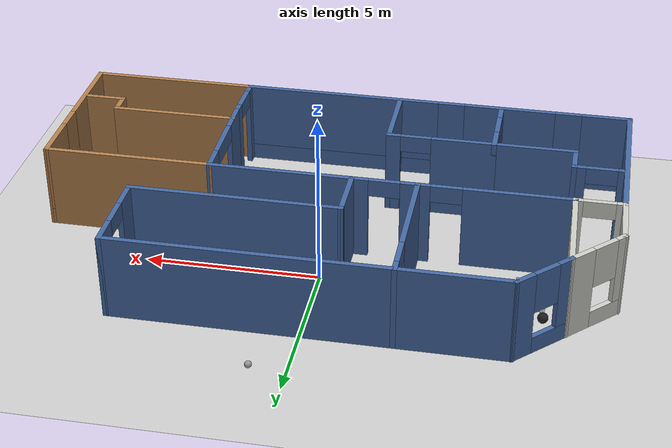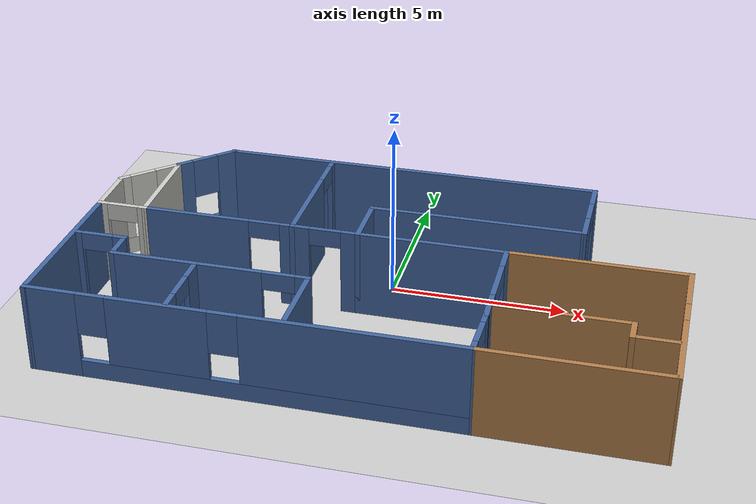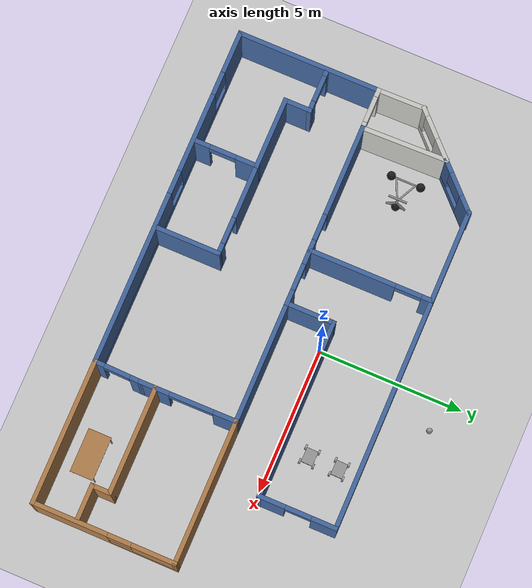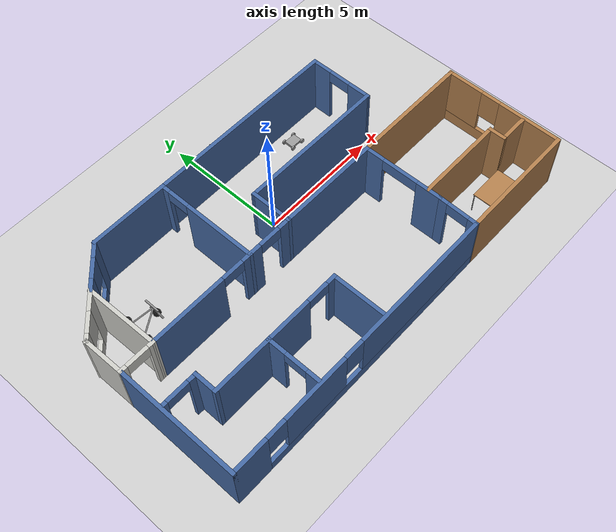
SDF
<sdf version="1.6">
 <world name="default">
  <plugin name="welcome_message" filename="libwelcome_message.so"/>
  <light name="sun" type="directional">
   <pose>0 0 10 0 -0 0</pose>
   <diffuse>0.8 0.8 0.8 1</diffuse>
   <specular>0.2 0.2 0.2 1</specular>
   <attenuation>
    <range>1000</range>
    <constant>0.9</constant>
    <linear>0.01</linear>
    <quadratic>0.001</quadratic>
   </attenuation>
   <direction>-0.5 0.1 -0.9</direction>
  </light>
  <model name="ground_plane">
   <static>1</static>
   <link name="link">
    <collision name="collision">
     <geometry><plane><normal>0 0 1</normal><size>100 100</size></plane></geometry>
     <surface>
      <contact><collide_bitmask>65535</collide_bitmask></contact>
      <friction><ode><mu>100</mu><mu2>50</mu2></ode></friction>
     </surface>
    </collision>
    <visual name="visual">
     <cast_shadows>0</cast_shadows>
     <geometry><plane><normal>0 0 1</normal><size>100 100</size></plane></geometry>
     <material>
      <script><uri>file://media/materials/scripts/gazebo.material</uri><name>Gazebo/Grey</name></script>
     </material>
    </visual>
   </link>
  </model>
  <gravity>0 0 -9.8</gravity>
  <magnetic_field>6e-06 2.3e-05 -4.2e-05</magnetic_field>
  <atmosphere type="adiabatic"/>
  <physics name="default_physics" default="0" type="ode">
   <max_step_size>0.001</max_step_size>
   <real_time_factor>1</real_time_factor>
   <real_time_update_rate>1000</real_time_update_rate>
  </physics>
  <scene><ambient>0.4 0.4 0.4 1</ambient><background>0.7 0.7 0.7 1</background><shadows>1</shadows></scene>
  <spherical_coordinates>
   <surface_model>EARTH_WGS84</surface_model>
   <latitude_deg>0</latitude_deg>
   <longitude_deg>0</longitude_deg>
   <elevation>0</elevation>
   <heading_deg>0</heading_deg>
  </spherical_coordinates>
  <model name="Building">
   <pose>0.01386 -1.75865 0 0 -0 0</pose>
   <link name="Wall_102">
    <pose>-2.84879 -2.32289 0 0 -0 0</pose>
    <visual name="Wall_102_Visual_0">
     <pose>-0.664345 0 1.25 0 -0 0</pose>
     <geometry><box><size>1.92131 0.15 2.5</size></box></geometry>
     <material>
      <script><uri>file://media/materials/scripts/gazebo.material</uri><name>Gazebo/Grey</name></script>
      <ambient>0.266667 0.407843 0.631373 1</ambient>
     </material>
     <meta><layer>0</layer></meta>
    </visual>
    <collision name="Wall_102_Collision_0">
     <geometry><box><size>1.92131 0.15 2.5</size></box></geometry>
     <pose>-0.664345 0 1.25 0 -0 0</pose>
    </collision>
    <visual name="Wall_102_Visual_1">
     <pose>1.41065 0 1.25 0 -0 0</pose>
     <geometry><box><size>0.42869 0.15 2.5</size></box></geometry>
     <material>
      <script><uri>file://media/materials/scripts/gazebo.material</uri><name>Gazebo/Grey</name></script>
      <ambient>0.266667 0.407843 0.631373 1</ambient>
     </material>
     <meta><layer>0</layer></meta>
    </visual>
    <collision name="Wall_102_Collision_1">
     <geometry><box><size>0.42869 0.15 2.5</size></box></geometry>
     <pose>1.41065 0 1.25 0 -0 0</pose>
    </collision>
    <visual name="Wall_102_Visual_2">
     <pose>0.74631 0 2.25 0 -0 0</pose>
     <geometry><box><size>0.9 0.15 0.5</size></box></geometry>
     <material>
      <script><uri>file://media/materials/scripts/gazebo.material</uri><name>Gazebo/Grey</name></script>
      <ambient>0.266667 0.407843 0.631373 1</ambient>
     </material>
     <meta><layer>0</layer></meta>
    </visual>
    <collision name="Wall_102_Collision_2">
     <geometry><box><size>0.9 0.15 0.5</size></box></geometry>
     <pose>0.74631 0 2.25 0 -0 0</pose>
    </collision>
   </link>
   <link name="Wall_104">
    <collision name="Wall_104_Collision">
     <geometry><box><size>2.5 0.15 2.5</size></box></geometry>
     <pose>0 0 1.25 0 -0 0</pose>
    </collision>
    <visual name="Wall_104_Visual">
     <pose>0 0 1.25 0 -0 0</pose>
     <geometry><box><size>2.5 0.15 2.5</size></box></geometry>
     <material>
      <script><uri>file://media/materials/scripts/gazebo.material</uri><name>Gazebo/Grey</name></script>
      <ambient>0.266667 0.407843 0.631373 1</ambient>
     </material>
     <meta><layer>0</layer></meta>
    </visual>
    <pose>-5.57379 -2.32289 0 0 -0 3.14159</pose>
   </link>
   <link name="Wall_105">
    <collision name="Wall_105_Collision">
     <geometry><box><size>1 0.15 2.5</size></box></geometry>
     <pose>0 0 1.25 0 -0 0</pose>
    </collision>
    <visual name="Wall_105_Visual">
     <pose>0 0 1.25 0 -0 0</pose>
     <geometry><box><size>1 0.15 2.5</size></box></geometry>
     <material>
      <script><uri>file://media/materials/scripts/gazebo.material</uri><name>Gazebo/Grey</name></script>
      <ambient>0.266667 0.407843 0.631373 1</ambient>
     </material>
     <meta><layer>0</layer></meta>
    </visual>
    <pose>-6.74879 -1.89789 0 0 -0 1.5708</pose>
   </link>
   <link name="Wall_106">
    <pose>-7.42379 -1.47289 0 0 -0 3.14159</pose>
    <visual name="Wall_106_Visual_0">
     <pose>-0.545893 0 1.25 0 -0 0</pose>
     <geometry><box><size>0.408214 0.15 2.5</size></box></geometry>
     <material>
      <script><uri>file://media/materials/scripts/gazebo.material</uri><name>Gazebo/Grey</name></script>
      <ambient>0.266667 0.407843 0.631373 1</ambient>
     </material>
     <meta><layer>0</layer></meta>
    </visual>
    <collision name="Wall_106_Collision_0">
     <geometry><box><size>0.408214 0.15 2.5</size></box></geometry>
     <pose>-0.545893 0 1.25 0 -0 0</pose>
    </collision>
    <visual name="Wall_106_Visual_1">
     <pose>0.654107 0 1.25 0 -0 0</pose>
     <geometry><box><size>0.191786 0.15 2.5</size></box></geometry>
     <material>
      <script><uri>file://media/materials/scripts/gazebo.material</uri><name>Gazebo/Grey</name></script>
      <ambient>0.266667 0.407843 0.631373 1</ambient>
     </material>
     <meta><layer>0</layer></meta>
    </visual>
    <collision name="Wall_106_Collision_1">
     <geometry><box><size>0.191786 0.15 2.5</size></box></geometry>
     <pose>0.654107 0 1.25 0 -0 0</pose>
    </collision>
    <visual name="Wall_106_Visual_2">
     <pose>0.108214 0 2.25 0 -0 0</pose>
     <geometry><box><size>0.9 0.15 0.5</size></box></geometry>
     <material>
      <script><uri>file://media/materials/scripts/gazebo.material</uri><name>Gazebo/Grey</name></script>
      <ambient>0.266667 0.407843 0.631373 1</ambient>
     </material>
     <meta><layer>0</layer></meta>
    </visual>
    <collision name="Wall_106_Collision_2">
     <geometry><box><size>0.9 0.15 0.5</size></box></geometry>
     <pose>0.108214 0 2.25 0 -0 0</pose>
    </collision>
   </link>
   <link name="Wall_110">
    <collision name="Wall_110_Collision">
     <geometry><box><size>5 0.15 2.5</size></box></geometry>
     <pose>0 0 1.25 0 -0 0</pose>
    </collision>
    <visual name="Wall_110_Visual">
     <pose>0 0 1.25 0 -0 0</pose>
     <geometry><box><size>5 0.15 2.5</size></box></geometry>
     <material>
      <script><uri>file://media/materials/scripts/gazebo.material</uri><name>Gazebo/Wood</name></script>
      <ambient>0.266667 0.407843 0.631373 1</ambient>
     </material>
     <meta><layer>0</layer></meta>
    </visual>
    <pose>5.84686 -4.53551 0 0 -0 3.14159</pose>
   </link>
   <link name="Wall_112">
    <collision name="Wall_112_Collision">
     <geometry><box><size>3.75 0.15 2.5</size></box></geometry>
     <pose>0 0 1.25 0 -0 0</pose>
    </collision>
    <visual name="Wall_112_Visual">
     <pose>0 0 1.25 0 -0 0</pose>
     <geometry><box><size>3.75 0.15 2.5</size></box></geometry>
     <material>
      <script><uri>file://media/materials/scripts/gazebo.material</uri><name>Gazebo/Wood</name></script>
      <ambient>0.266667 0.407843 0.631373 1</ambient>
     </material>
     <meta><layer>0</layer></meta>
    </visual>
    <pose>5.25889 -2.43595 0 0 -0 0</pose>
   </link>
   <link name="Wall_113">
    <collision name="Wall_113_Collision">
     <geometry><box><size>0.75 0.15 2.5</size></box></geometry>
     <pose>0 0 1.25 0 -0 0</pose>
    </collision>
    <visual name="Wall_113_Visual">
     <pose>0 0 1.25 0 -0 0</pose>
     <geometry><box><size>0.75 0.15 2.5</size></box></geometry>
     <material>
      <script><uri>file://media/materials/scripts/gazebo.material</uri><name>Gazebo/Wood</name></script>
      <ambient>0.266667 0.407843 0.631373 1</ambient>
     </material>
     <meta><layer>0</layer></meta>
    </visual>
    <pose>7.05889 -2.73595 0 0 0 -1.5708</pose>
   </link>
   <link name="Wall_114">
    <collision name="Wall_114_Collision">
     <geometry><box><size>1.25 0.15 2.5</size></box></geometry>
     <pose>0 0 1.25 0 -0 0</pose>
    </collision>
    <visual name="Wall_114_Visual">
     <pose>0 0 1.25 0 -0 0</pose>
     <geometry><box><size>1.25 0.15 2.5</size></box></geometry>
     <material>
      <script><uri>file://media/materials/scripts/gazebo.material</uri><name>Gazebo/Wood</name></script>
      <ambient>0.266667 0.407843 0.631373 1</ambient>
     </material>
     <meta><layer>0</layer></meta>
    </visual>
    <pose>7.60889 -3.03595 0 0 -0 0</pose>
   </link>
   <link name="Wall_38">
    <collision name="Wall_38_Collision">
     <geometry><box><size>8 0.15 2.5</size></box></geometry>
     <pose>0 0 1.25 0 -0 0</pose>
    </collision>
    <visual name="Wall_38_Visual">
     <pose>0 0 1.25 0 -0 0</pose>
     <geometry><box><size>8 0.15 2.5</size></box></geometry>
     <material>
      <script><uri>file://media/materials/scripts/gazebo.material</uri><name>Gazebo/Grey</name></script>
      <ambient>0.266667 0.407843 0.631373 1</ambient>
     </material>
     <meta><layer>0</layer></meta>
    </visual>
    <pose>1.38708 4.50609 0 0 -0 0</pose>
   </link>
   <link name="Wall_45">
    <pose>-1.58992 0.314341 0 0 -0 0</pose>
    <visual name="Wall_45_Visual_0">
     <pose>-0.726162 0 1.25 0 -0 0</pose>
     <geometry><box><size>0.547677 0.15 2.5</size></box></geometry>
     <material>
      <script><uri>file://media/materials/scripts/gazebo.material</uri><name>Gazebo/Grey</name></script>
      <ambient>0.266667 0.407843 0.631373 1</ambient>
     </material>
     <meta><layer>0</layer></meta>
    </visual>
    <collision name="Wall_45_Collision_0">
     <geometry><box><size>0.547677 0.15 2.5</size></box></geometry>
     <pose>-0.726162 0 1.25 0 -0 0</pose>
    </collision>
    <visual name="Wall_45_Visual_1">
     <pose>0.723838 0 1.25 0 -0 0</pose>
     <geometry><box><size>0.552323 0.15 2.5</size></box></geometry>
     <material>
      <script><uri>file://media/materials/scripts/gazebo.material</uri><name>Gazebo/Grey</name></script>
      <ambient>0.266667 0.407843 0.631373 1</ambient>
     </material>
     <meta><layer>0</layer></meta>
    </visual>
    <collision name="Wall_45_Collision_1">
     <geometry><box><size>0.552323 0.15 2.5</size></box></geometry>
     <pose>0.723838 0 1.25 0 -0 0</pose>
    </collision>
    <visual name="Wall_45_Visual_2">
     <pose>-0.002323 0 2.25 0 -0 0</pose>
     <geometry><box><size>0.9 0.15 0.5</size></box></geometry>
     <material>
      <script><uri>file://media/materials/scripts/gazebo.material</uri><name>Gazebo/Grey</name></script>
      <ambient>0.266667 0.407843 0.631373 1</ambient>
     </material>
     <meta><layer>0</layer></meta>
    </visual>
    <collision name="Wall_45_Collision_2">
     <geometry><box><size>0.9 0.15 0.5</size></box></geometry>
     <pose>-0.002323 0 2.25 0 -0 0</pose>
    </collision>
   </link>
   <link name="Wall_47">
    <pose>-2.53403 2.41022 0 0 0 -1.56894</pose>
    <visual name="Wall_47_Visual_0">
     <pose>-1.96327 0 1.25 0 -0 0</pose>
     <geometry><box><size>0.415543 0.15 2.5</size></box></geometry>
     <material>
      <script><uri>file://media/materials/scripts/gazebo.material</uri><name>Gazebo/Grey</name></script>
      <ambient>0.266667 0.407843 0.631373 1</ambient>
     </material>
     <meta><layer>0</layer></meta>
    </visual>
    <collision name="Wall_47_Collision_0">
     <geometry><box><size>0.415543 0.15 2.5</size></box></geometry>
     <pose>-1.96327 0 1.25 0 -0 0</pose>
    </collision>
    <visual name="Wall_47_Visual_1">
     <pose>0.657772 0 1.25 0 -0 0</pose>
     <geometry><box><size>3.02655 0.15 2.5</size></box></geometry>
     <material>
      <script><uri>file://media/materials/scripts/gazebo.material</uri><name>Gazebo/Grey</name></script>
      <ambient>0.266667 0.407843 0.631373 1</ambient>
     </material>
     <meta><layer>0</layer></meta>
    </visual>
    <collision name="Wall_47_Collision_1">
     <geometry><box><size>3.02655 0.15 2.5</size></box></geometry>
     <pose>0.657772 0 1.25 0 -0 0</pose>
    </collision>
    <visual name="Wall_47_Visual_2">
     <pose>-1.3055 0 2.25 0 -0 0</pose>
     <geometry><box><size>0.9 0.15 0.5</size></box></geometry>
     <material>
      <script><uri>file://media/materials/scripts/gazebo.material</uri><name>Gazebo/Grey</name></script>
      <ambient>0.266667 0.407843 0.631373 1</ambient>
     </material>
     <meta><layer>0</layer></meta>
    </visual>
    <collision name="Wall_47_Collision_2">
     <geometry><box><size>0.9 0.15 0.5</size></box></geometry>
     <pose>-1.3055 0 2.25 0 -0 0</pose>
    </collision>
   </link>
   <link name="Wall_49">
    <collision name="Wall_49_Collision">
     <geometry><box><size>1.75 0.15 2.5</size></box></geometry>
     <pose>0 0 1.25 0 -0 0</pose>
    </collision>
    <visual name="Wall_49_Visual">
     <pose>0 0 1.25 0 -0 0</pose>
     <geometry><box><size>1.75 0.15 2.5</size></box></geometry>
     <material>
      <script><uri>file://media/materials/scripts/gazebo.material</uri><name>Gazebo/Grey</name></script>
      <ambient>0.266667 0.407843 0.631373 1</ambient>
     </material>
     <meta><layer>0</layer></meta>
    </visual>
    <pose>-0.664918 1.11434 0 0 -0 1.5708</pose>
   </link>
   <link name="Wall_53">
    <pose>5.31208 3.20609 0 0 0 -1.5708</pose>
    <visual name="Wall_53_Visual_0">
     <pose>-0.926931 0 1.25 0 -0 0</pose>
     <geometry><box><size>0.896138 0.15 2.5</size></box></geometry>
     <material>
      <script><uri>file://media/materials/scripts/gazebo.material</uri><name>Gazebo/Grey</name></script>
      <ambient>0.266667 0.407843 0.631373 1</ambient>
     </material>
     <meta><layer>0</layer></meta>
    </visual>
    <collision name="Wall_53_Collision_0">
     <geometry><box><size>0.896138 0.15 2.5</size></box></geometry>
     <pose>-0.926931 0 1.25 0 -0 0</pose>
    </collision>
    <visual name="Wall_53_Visual_1">
     <pose>0.898069 0 1.25 0 -0 0</pose>
     <geometry><box><size>0.953862 0.15 2.5</size></box></geometry>
     <material>
      <script><uri>file://media/materials/scripts/gazebo.material</uri><name>Gazebo/Grey</name></script>
      <ambient>0.266667 0.407843 0.631373 1</ambient>
     </material>
     <meta><layer>0</layer></meta>
    </visual>
    <collision name="Wall_53_Collision_1">
     <geometry><box><size>0.953862 0.15 2.5</size></box></geometry>
     <pose>0.898069 0 1.25 0 -0 0</pose>
    </collision>
    <visual name="Wall_53_Visual_2">
     <pose>-0.028862 0 2.25 0 -0 0</pose>
     <geometry><box><size>0.9 0.15 0.5</size></box></geometry>
     <material>
      <script><uri>file://media/materials/scripts/gazebo.material</uri><name>Gazebo/Grey</name></script>
      <ambient>0.266667 0.407843 0.631373 1</ambient>
     </material>
     <meta><layer>0</layer></meta>
    </visual>
    <collision name="Wall_53_Collision_2">
     <geometry><box><size>0.9 0.15 0.5</size></box></geometry>
     <pose>-0.028862 0 2.25 0 -0 0</pose>
    </collision>
   </link>
   <link name="Wall_54">
    <collision name="Wall_54_Collision">
     <geometry><box><size>6.127 0.15 2.5</size></box></geometry>
     <pose>0 0 1.25 0 -0 0</pose>
    </collision>
    <visual name="Wall_54_Visual">
     <pose>0 0 1.25 0 -0 0</pose>
     <geometry><box><size>6.127 0.15 2.5</size></box></geometry>
     <material>
      <script><uri>file://media/materials/scripts/gazebo.material</uri><name>Gazebo/Grey</name></script>
      <ambient>0.266667 0.407843 0.631373 1</ambient>
     </material>
     <meta><layer>0</layer></meta>
    </visual>
    <pose>2.32358 1.91022 0 0 -0 3.14021</pose>
   </link>
   <link name="Wall_56">
    <collision name="Wall_56_Collision">
     <geometry><box><size>4.25 0.15 2.5</size></box></geometry>
     <pose>0 0 1.25 0 -0 0</pose>
    </collision>
    <visual name="Wall_56_Visual">
     <pose>0 0 1.25 0 -0 0</pose>
     <geometry><box><size>4.25 0.15 2.5</size></box></geometry>
     <material>
      <script><uri>file://media/materials/scripts/gazebo.material</uri><name>Gazebo/Grey</name></script>
      <ambient>0.266667 0.407843 0.631373 1</ambient>
     </material>
     <meta><layer>0</layer></meta>
    </visual>
    <pose>1.38508 0.314341 0 0 -0 0</pose>
   </link>
   <link name="Wall_59">
    <pose>8.27847 -2.11058 0 0 -0 1.56807</pose>
    <visual name="Wall_59_Visual_0">
     <pose>-1.18175 0 1.25 0 -0 0</pose>
     <geometry><box><size>2.63637 0.15 2.5</size></box></geometry>
     <material>
      <script><uri>file://media/materials/scripts/gazebo.material</uri><name>Gazebo/Wood</name></script>
      <ambient>0.266667 0.407843 0.631373 1</ambient>
     </material>
     <meta><layer>0</layer></meta>
    </visual>
    <collision name="Wall_59_Collision_0">
     <geometry><box><size>2.63637 0.15 2.5</size></box></geometry>
     <pose>-1.18175 0 1.25 0 -0 0</pose>
    </collision>
    <visual name="Wall_59_Visual_1">
     <pose>1.31819 0 0.25 0 -0 0</pose>
     <geometry><box><size>2.36349 0.15 0.5</size></box></geometry>
     <material>
      <script><uri>file://media/materials/scripts/gazebo.material</uri><name>Gazebo/Wood</name></script>
      <ambient>0.266667 0.407843 0.631373 1</ambient>
     </material>
     <meta><layer>0</layer></meta>
    </visual>
    <collision name="Wall_59_Collision_1">
     <geometry><box><size>2.36349 0.15 0.5</size></box></geometry>
     <pose>1.31819 0 0.25 0 -0 0</pose>
    </collision>
    <visual name="Wall_59_Visual_2">
     <pose>1.71819 0 1.5 0 -0 0</pose>
     <geometry><box><size>1.5635 0.15 2</size></box></geometry>
     <material>
      <script><uri>file://media/materials/scripts/gazebo.material</uri><name>Gazebo/Wood</name></script>
      <ambient>0.266667 0.407843 0.631373 1</ambient>
     </material>
     <meta><layer>0</layer></meta>
    </visual>
    <collision name="Wall_59_Collision_2">
     <geometry><box><size>1.5635 0.15 2</size></box></geometry>
     <pose>1.71819 0 1.5 0 -0 0</pose>
    </collision>
    <visual name="Wall_59_Visual_3">
     <pose>0.536439 0 1.9 0 -0 0</pose>
     <geometry><box><size>0.8 0.15 1.2</size></box></geometry>
     <material>
      <script><uri>file://media/materials/scripts/gazebo.material</uri><name>Gazebo/Wood</name></script>
      <ambient>0.266667 0.407843 0.631373 1</ambient>
     </material>
     <meta><layer>0</layer></meta>
    </visual>
    <collision name="Wall_59_Collision_3">
     <geometry><box><size>0.8 0.15 1.2</size></box></geometry>
     <pose>0.536439 0 1.9 0 -0 0</pose>
    </collision>
   </link>
   <link name="Wall_60">
    <collision name="Wall_60_Collision">
     <geometry><box><size>5 0.15 2.5</size></box></geometry>
     <pose>0 0 1.25 0 -0 0</pose>
    </collision>
    <visual name="Wall_60_Visual">
     <pose>0 0 1.25 0 -0 0</pose>
     <geometry><box><size>5 0.15 2.5</size></box></geometry>
     <material>
      <script><uri>file://media/materials/scripts/gazebo.material</uri><name>Gazebo/Wood</name></script>
      <ambient>0.266667 0.407843 0.631373 1</ambient>
     </material>
     <meta><layer>0</layer></meta>
    </visual>
    <pose>5.86008 0.314341 0 0 -0 3.14159</pose>
   </link>
   <link name="Wall_64">
    <pose>-4.70513 0.314341 0 0 -0 3.14159</pose>
    <visual name="Wall_64_Visual_0">
     <pose>-2.03246 0 1.25 0 -0 0</pose>
     <geometry><box><size>0.435078 0.15 2.5</size></box></geometry>
     <material>
      <script><uri>file://media/materials/scripts/gazebo.material</uri><name>Gazebo/Grey</name></script>
      <ambient>0.266667 0.407843 0.631373 1</ambient>
     </material>
     <meta><layer>0</layer></meta>
    </visual>
    <collision name="Wall_64_Collision_0">
     <geometry><box><size>0.435078 0.15 2.5</size></box></geometry>
     <pose>-2.03246 0 1.25 0 -0 0</pose>
    </collision>
    <visual name="Wall_64_Visual_1">
     <pose>0.667539 0 1.25 0 -0 0</pose>
     <geometry><box><size>3.16492 0.15 2.5</size></box></geometry>
     <material>
      <script><uri>file://media/materials/scripts/gazebo.material</uri><name>Gazebo/Grey</name></script>
      <ambient>0.266667 0.407843 0.631373 1</ambient>
     </material>
     <meta><layer>0</layer></meta>
    </visual>
    <collision name="Wall_64_Collision_1">
     <geometry><box><size>3.16492 0.15 2.5</size></box></geometry>
     <pose>0.667539 0 1.25 0 -0 0</pose>
    </collision>
    <visual name="Wall_64_Visual_2">
     <pose>-1.36492 0 2.25 0 -0 0</pose>
     <geometry><box><size>0.9 0.15 0.5</size></box></geometry>
     <material>
      <script><uri>file://media/materials/scripts/gazebo.material</uri><name>Gazebo/Grey</name></script>
      <ambient>0.266667 0.407843 0.631373 1</ambient>
     </material>
     <meta><layer>0</layer></meta>
    </visual>
    <collision name="Wall_64_Collision_2">
     <geometry><box><size>0.9 0.15 0.5</size></box></geometry>
     <pose>-1.36492 0 2.25 0 -0 0</pose>
    </collision>
   </link>
   <link name="Wall_73">
    <collision name="Wall_73_Collision">
     <geometry><box><size>3.25 0.15 2.5</size></box></geometry>
     <pose>0 0 1.25 0 -0 0</pose>
    </collision>
    <visual name="Wall_73_Visual">
     <pose>0 0 1.25 0 -0 0</pose>
     <geometry><box><size>3.25 0.15 2.5</size></box></geometry>
     <material>
      <script><uri>file://media/materials/scripts/gazebo.material</uri><name>Gazebo/Grey</name></script>
      <ambient>0.266667 0.407843 0.631373 1</ambient>
     </material>
     <meta><layer>0</layer></meta>
    </visual>
    <pose>-4.08793 4.50609 0 0 -0 3.14159</pose>
   </link>
   <link name="Wall_74">
    <pose>-6.292 3.85202 0 0 0 -2.35619</pose>
    <visual name="Wall_74_Visual_0">
     <pose>-0.659149 0 1.25 0 -0 0</pose>
     <geometry><box><size>0.681703 0.15 2.5</size></box></geometry>
     <material>
      <script><uri>file://media/materials/scripts/gazebo.material</uri><name>Gazebo/Grey</name></script>
      <ambient>0.266667 0.407843 0.631373 1</ambient>
     </material>
     <meta><layer>0</layer></meta>
    </visual>
    <collision name="Wall_74_Collision_0">
     <geometry><box><size>0.681703 0.15 2.5</size></box></geometry>
     <pose>-0.659149 0 1.25 0 -0 0</pose>
    </collision>
    <visual name="Wall_74_Visual_1">
     <pose>0.340851 0 0.25 0 -0 0</pose>
     <geometry><box><size>1.3183 0.15 0.5</size></box></geometry>
     <material>
      <script><uri>file://media/materials/scripts/gazebo.material</uri><name>Gazebo/Grey</name></script>
      <ambient>0.266667 0.407843 0.631373 1</ambient>
     </material>
     <meta><layer>0</layer></meta>
    </visual>
    <collision name="Wall_74_Collision_1">
     <geometry><box><size>1.3183 0.15 0.5</size></box></geometry>
     <pose>0.340851 0 0.25 0 -0 0</pose>
    </collision>
    <visual name="Wall_74_Visual_2">
     <pose>0.740851 0 1.5 0 -0 0</pose>
     <geometry><box><size>0.518297 0.15 2</size></box></geometry>
     <material>
      <script><uri>file://media/materials/scripts/gazebo.material</uri><name>Gazebo/Grey</name></script>
      <ambient>0.266667 0.407843 0.631373 1</ambient>
     </material>
     <meta><layer>0</layer></meta>
    </visual>
    <collision name="Wall_74_Collision_2">
     <geometry><box><size>0.518297 0.15 2</size></box></geometry>
     <pose>0.740851 0 1.5 0 -0 0</pose>
    </collision>
    <visual name="Wall_74_Visual_3">
     <pose>0.081703 0 1.9 0 -0 0</pose>
     <geometry><box><size>0.8 0.15 1.2</size></box></geometry>
     <material>
      <script><uri>file://media/materials/scripts/gazebo.material</uri><name>Gazebo/Grey</name></script>
      <ambient>0.266667 0.407843 0.631373 1</ambient>
     </material>
     <meta><layer>0</layer></meta>
    </visual>
    <collision name="Wall_74_Collision_3">
     <geometry><box><size>0.8 0.15 1.2</size></box></geometry>
     <pose>0.081703 0 1.9 0 -0 0</pose>
    </collision>
   </link>
   <link name="Wall_75">
    <collision name="Wall_75_Collision">
     <geometry><box><size>3.03436 0.15 2.5</size></box></geometry>
     <pose>0 0 1.25 0 -0 0</pose>
    </collision>
    <visual name="Wall_75_Visual">
     <pose>0 0 1.25 0 -0 0</pose>
     <geometry><box><size>3.03436 0.15 2.5</size></box></geometry>
     <material>
      <script><uri>file://media/materials/scripts/gazebo.material</uri><name>Gazebo/CeilingTiled</name></script>
      <ambient>0.266667 0.407843 0.631373 1</ambient>
     </material>
     <meta><layer>0</layer></meta>
    </visual>
    <pose>-6.9131 1.75614 0 0 0 -1.54793</pose>
   </link>
   <link name="Wall_77">
    <pose>-7.55513 0.314341 0 0 -0 3.14159</pose>
    <visual name="Wall_77_Visual_0">
     <pose>-0.606045 0 1.25 0 -0 0</pose>
     <geometry><box><size>0.28791 0.15 2.5</size></box></geometry>
     <material>
      <script><uri>file://media/materials/scripts/gazebo.material</uri><name>Gazebo/CeilingTiled</name></script>
      <ambient>0.266667 0.407843 0.631373 1</ambient>
     </material>
     <meta><layer>0</layer></meta>
    </visual>
    <collision name="Wall_77_Collision_0">
     <geometry><box><size>0.28791 0.15 2.5</size></box></geometry>
     <pose>-0.606045 0 1.25 0 -0 0</pose>
    </collision>
    <visual name="Wall_77_Visual_1">
     <pose>0.593955 0 1.25 0 -0 0</pose>
     <geometry><box><size>0.31209 0.15 2.5</size></box></geometry>
     <material>
      <script><uri>file://media/materials/scripts/gazebo.material</uri><name>Gazebo/CeilingTiled</name></script>
      <ambient>0.266667 0.407843 0.631373 1</ambient>
     </material>
     <meta><layer>0</layer></meta>
    </visual>
    <collision name="Wall_77_Collision_1">
     <geometry><box><size>0.31209 0.15 2.5</size></box></geometry>
     <pose>0.593955 0 1.25 0 -0 0</pose>
    </collision>
    <visual name="Wall_77_Visual_2">
     <pose>-0.01209 0 2.25 0 -0 0</pose>
     <geometry><box><size>0.9 0.15 0.5</size></box></geometry>
     <material>
      <script><uri>file://media/materials/scripts/gazebo.material</uri><name>Gazebo/CeilingTiled</name></script>
      <ambient>0.266667 0.407843 0.631373 1</ambient>
     </material>
     <meta><layer>0</layer></meta>
    </visual>
    <collision name="Wall_77_Collision_2">
     <geometry><box><size>0.9 0.15 0.5</size></box></geometry>
     <pose>-0.01209 0 2.25 0 -0 0</pose>
    </collision>
   </link>
   <link name="Wall_78">
    <collision name="Wall_78_Collision">
     <geometry><box><size>5 0.15 2.5</size></box></geometry>
     <pose>0 0 1.25 0 -0 0</pose>
    </collision>
    <visual name="Wall_78_Visual">
     <pose>0 0 1.25 0 -0 0</pose>
     <geometry><box><size>5 0.15 2.5</size></box></geometry>
     <material>
      <script><uri>file://media/materials/scripts/gazebo.material</uri><name>Gazebo/Grey</name></script>
      <ambient>0.266667 0.407843 0.631373 1</ambient>
     </material>
     <meta><layer>0</layer></meta>
    </visual>
    <pose>-8.23013 -2.11066 0 0 0 -1.5708</pose>
   </link>
   <link name="Wall_79">
    <pose>-2.43013 -4.53566 0 0 -0 0</pose>
    <visual name="Wall_79_Visual_0">
     <pose>-5.13095 0 1.25 0 -0 0</pose>
     <geometry><box><size>1.48809 0.15 2.5</size></box></geometry>
     <material>
      <script><uri>file://media/materials/scripts/gazebo.material</uri><name>Gazebo/Grey</name></script>
      <ambient>0.266667 0.407843 0.631373 1</ambient>
     </material>
     <meta><layer>0</layer></meta>
    </visual>
    <collision name="Wall_79_Collision_0">
     <geometry><box><size>1.48809 0.15 2.5</size></box></geometry>
     <pose>-5.13095 0 1.25 0 -0 0</pose>
    </collision>
    <visual name="Wall_79_Visual_1">
     <pose>0.744046 0 0.25 0 -0 0</pose>
     <geometry><box><size>10.2619 0.15 0.5</size></box></geometry>
     <material>
      <script><uri>file://media/materials/scripts/gazebo.material</uri><name>Gazebo/Grey</name></script>
      <ambient>0.266667 0.407843 0.631373 1</ambient>
     </material>
     <meta><layer>0</layer></meta>
    </visual>
    <collision name="Wall_79_Collision_1">
     <geometry><box><size>10.2619 0.15 0.5</size></box></geometry>
     <pose>0.744046 0 0.25 0 -0 0</pose>
    </collision>
    <visual name="Wall_79_Visual_2">
     <pose>-2.21742 0 1.5 0 -0 0</pose>
     <geometry><box><size>2.73898 0.15 2</size></box></geometry>
     <material>
      <script><uri>file://media/materials/scripts/gazebo.material</uri><name>Gazebo/Grey</name></script>
      <ambient>0.266667 0.407843 0.631373 1</ambient>
     </material>
     <meta><layer>0</layer></meta>
    </visual>
    <collision name="Wall_79_Collision_2">
     <geometry><box><size>2.73898 0.15 2</size></box></geometry>
     <pose>-2.21742 0 1.5 0 -0 0</pose>
    </collision>
    <visual name="Wall_79_Visual_3">
     <pose>2.91354 0 1.5 0 -0 0</pose>
     <geometry><box><size>5.92292 0.15 2</size></box></geometry>
     <material>
      <script><uri>file://media/materials/scripts/gazebo.material</uri><name>Gazebo/Grey</name></script>
      <ambient>0.266667 0.407843 0.631373 1</ambient>
     </material>
     <meta><layer>0</layer></meta>
    </visual>
    <collision name="Wall_79_Collision_3">
     <geometry><box><size>5.92292 0.15 2</size></box></geometry>
     <pose>2.91354 0 1.5 0 -0 0</pose>
    </collision>
    <visual name="Wall_79_Visual_4">
     <pose>-3.98691 0 1.9 0 -0 0</pose>
     <geometry><box><size>0.8 0.15 1.2</size></box></geometry>
     <material>
      <script><uri>file://media/materials/scripts/gazebo.material</uri><name>Gazebo/Grey</name></script>
      <ambient>0.266667 0.407843 0.631373 1</ambient>
     </material>
     <meta><layer>0</layer></meta>
    </visual>
    <collision name="Wall_79_Collision_4">
     <geometry><box><size>0.8 0.15 1.2</size></box></geometry>
     <pose>-3.98691 0 1.9 0 -0 0</pose>
    </collision>
    <visual name="Wall_79_Visual_5">
     <pose>-0.447924 0 1.9 0 -0 0</pose>
     <geometry><box><size>0.8 0.15 1.2</size></box></geometry>
     <material>
      <script><uri>file://media/materials/scripts/gazebo.material</uri><name>Gazebo/Grey</name></script>
      <ambient>0.266667 0.407843 0.631373 1</ambient>
     </material>
     <meta><layer>0</layer></meta>
    </visual>
    <collision name="Wall_79_Collision_5">
     <geometry><box><size>0.8 0.15 1.2</size></box></geometry>
     <pose>-0.447924 0 1.9 0 -0 0</pose>
    </collision>
   </link>
   <link name="Wall_81">
    <pose>-7.60015 2.54387 0 0 0 -2.35619</pose>
    <visual name="Wall_81_Visual_0">
     <pose>-0.578266 0 1.25 0 -0 0</pose>
     <geometry><box><size>0.843467 0.15 2.5</size></box></geometry>
     <material>
      <script><uri>file://media/materials/scripts/gazebo.material</uri><name>Gazebo/CeilingTiled</name></script>
      <ambient>0.266667 0.407843 0.631373 1</ambient>
     </material>
     <meta><layer>0</layer></meta>
    </visual>
    <collision name="Wall_81_Collision_0">
     <geometry><box><size>0.843467 0.15 2.5</size></box></geometry>
     <pose>-0.578266 0 1.25 0 -0 0</pose>
    </collision>
    <visual name="Wall_81_Visual_1">
     <pose>0.421734 0 0.25 0 -0 0</pose>
     <geometry><box><size>1.15653 0.15 0.5</size></box></geometry>
     <material>
      <script><uri>file://media/materials/scripts/gazebo.material</uri><name>Gazebo/CeilingTiled</name></script>
      <ambient>0.266667 0.407843 0.631373 1</ambient>
     </material>
     <meta><layer>0</layer></meta>
    </visual>
    <collision name="Wall_81_Collision_1">
     <geometry><box><size>1.15653 0.15 0.5</size></box></geometry>
     <pose>0.421734 0 0.25 0 -0 0</pose>
    </collision>
    <visual name="Wall_81_Visual_2">
     <pose>0.821734 0 1.5 0 -0 0</pose>
     <geometry><box><size>0.356533 0.15 2</size></box></geometry>
     <material>
      <script><uri>file://media/materials/scripts/gazebo.material</uri><name>Gazebo/CeilingTiled</name></script>
      <ambient>0.266667 0.407843 0.631373 1</ambient>
     </material>
     <meta><layer>0</layer></meta>
    </visual>
    <collision name="Wall_81_Collision_2">
     <geometry><box><size>0.356533 0.15 2</size></box></geometry>
     <pose>0.821734 0 1.5 0 -0 0</pose>
    </collision>
    <visual name="Wall_81_Visual_3">
     <pose>0.243467 0 1.9 0 -0 0</pose>
     <geometry><box><size>0.8 0.15 1.2</size></box></geometry>
     <material>
      <script><uri>file://media/materials/scripts/gazebo.material</uri><name>Gazebo/CeilingTiled</name></script>
      <ambient>0.266667 0.407843 0.631373 1</ambient>
     </material>
     <meta><layer>0</layer></meta>
    </visual>
    <collision name="Wall_81_Collision_3">
     <geometry><box><size>0.8 0.15 1.2</size></box></geometry>
     <pose>0.243467 0 1.9 0 -0 0</pose>
    </collision>
   </link>
   <link name="Wall_82">
    <collision name="Wall_82_Collision">
     <geometry><box><size>1.72564 0.15 2.5</size></box></geometry>
     <pose>0 0 1.25 0 -0 0</pose>
    </collision>
    <visual name="Wall_82_Visual">
     <pose>0 0 1.25 0 -0 0</pose>
     <geometry><box><size>1.72564 0.15 2.5</size></box></geometry>
     <material>
      <script><uri>file://media/materials/scripts/gazebo.material</uri><name>Gazebo/CeilingTiled</name></script>
      <ambient>0.266667 0.407843 0.631373 1</ambient>
     </material>
     <meta><layer>0</layer></meta>
    </visual>
    <pose>-8.24217 1.10207 0 0 0 -1.5555</pose>
   </link>
   <link name="Wall_90">
    <pose>-4.39879 -3.37289 0 0 0 -1.5708</pose>
    <visual name="Wall_90_Visual_0">
     <pose>-0.725857 0 1.25 0 -0 0</pose>
     <geometry><box><size>0.798287 0.15 2.5</size></box></geometry>
     <material>
      <script><uri>file://media/materials/scripts/gazebo.material</uri><name>Gazebo/Grey</name></script>
      <ambient>0.266667 0.407843 0.631373 1</ambient>
     </material>
     <meta><layer>0</layer></meta>
    </visual>
    <collision name="Wall_90_Collision_0">
     <geometry><box><size>0.798287 0.15 2.5</size></box></geometry>
     <pose>-0.725857 0 1.25 0 -0 0</pose>
    </collision>
    <visual name="Wall_90_Visual_1">
     <pose>0.849143 0 1.25 0 -0 0</pose>
     <geometry><box><size>0.551713 0.15 2.5</size></box></geometry>
     <material>
      <script><uri>file://media/materials/scripts/gazebo.material</uri><name>Gazebo/Grey</name></script>
      <ambient>0.266667 0.407843 0.631373 1</ambient>
     </material>
     <meta><layer>0</layer></meta>
    </visual>
    <collision name="Wall_90_Collision_1">
     <geometry><box><size>0.551713 0.15 2.5</size></box></geometry>
     <pose>0.849143 0 1.25 0 -0 0</pose>
    </collision>
    <visual name="Wall_90_Visual_2">
     <pose>0.123287 0 2.25 0 -0 0</pose>
     <geometry><box><size>0.9 0.15 0.5</size></box></geometry>
     <material>
      <script><uri>file://media/materials/scripts/gazebo.material</uri><name>Gazebo/Grey</name></script>
      <ambient>0.266667 0.407843 0.631373 1</ambient>
     </material>
     <meta><layer>0</layer></meta>
    </visual>
    <collision name="Wall_90_Collision_2">
     <geometry><box><size>0.9 0.15 0.5</size></box></geometry>
     <pose>0.123287 0 2.25 0 -0 0</pose>
    </collision>
   </link>
   <link name="Wall_92">
    <pose>3.44771 -1.31902 0 0 -0 1.57853</pose>
    <visual name="Wall_92_Visual_0">
     <pose>-1.17707 0 1.25 0 -0 0</pose>
     <geometry><box><size>1.06278 0.15 2.5</size></box></geometry>
     <material>
      <script><uri>file://media/materials/scripts/gazebo.material</uri><name>Gazebo/Grey</name></script>
      <ambient>0.266667 0.407843 0.631373 1</ambient>
     </material>
     <meta><layer>0</layer></meta>
    </visual>
    <collision name="Wall_92_Collision_0">
     <geometry><box><size>1.06278 0.15 2.5</size></box></geometry>
     <pose>-1.17707 0 1.25 0 -0 0</pose>
    </collision>
    <visual name="Wall_92_Visual_1">
     <pose>1.28139 0 1.25 0 -0 0</pose>
     <geometry><box><size>0.854133 0.15 2.5</size></box></geometry>
     <material>
      <script><uri>file://media/materials/scripts/gazebo.material</uri><name>Gazebo/Grey</name></script>
      <ambient>0.266667 0.407843 0.631373 1</ambient>
     </material>
     <meta><layer>0</layer></meta>
    </visual>
    <collision name="Wall_92_Collision_1">
     <geometry><box><size>0.854133 0.15 2.5</size></box></geometry>
     <pose>1.28139 0 1.25 0 -0 0</pose>
    </collision>
    <visual name="Wall_92_Visual_2">
     <pose>0.104324 0 2.25 0 -0 0</pose>
     <geometry><box><size>1.5 0.15 0.5</size></box></geometry>
     <material>
      <script><uri>file://media/materials/scripts/gazebo.material</uri><name>Gazebo/Grey</name></script>
      <ambient>0.266667 0.407843 0.631373 1</ambient>
     </material>
     <meta><layer>0</layer></meta>
    </visual>
    <collision name="Wall_92_Collision_2">
     <geometry><box><size>1.5 0.15 0.5</size></box></geometry>
     <pose>0.104324 0 2.25 0 -0 0</pose>
    </collision>
   </link>
   <link name="Wall_94">
    <pose>3.44109 -3.74394 0 0 0 -1.5951</pose>
    <visual name="Wall_94_Visual_0">
     <pose>-0.64956 0 1.25 0 -0 0</pose>
     <geometry><box><size>0.434175 0.15 2.5</size></box></geometry>
     <material>
      <script><uri>file://media/materials/scripts/gazebo.material</uri><name>Gazebo/Grey</name></script>
      <ambient>0.266667 0.407843 0.631373 1</ambient>
     </material>
     <meta><layer>0</layer></meta>
    </visual>
    <collision name="Wall_94_Collision_0">
     <geometry><box><size>0.434175 0.15 2.5</size></box></geometry>
     <pose>-0.64956 0 1.25 0 -0 0</pose>
    </collision>
    <visual name="Wall_94_Visual_1">
     <pose>0.667087 0 1.25 0 -0 0</pose>
     <geometry><box><size>0.399121 0.15 2.5</size></box></geometry>
     <material>
      <script><uri>file://media/materials/scripts/gazebo.material</uri><name>Gazebo/Grey</name></script>
      <ambient>0.266667 0.407843 0.631373 1</ambient>
     </material>
     <meta><layer>0</layer></meta>
    </visual>
    <collision name="Wall_94_Collision_1">
     <geometry><box><size>0.399121 0.15 2.5</size></box></geometry>
     <pose>0.667087 0 1.25 0 -0 0</pose>
    </collision>
    <visual name="Wall_94_Visual_2">
     <pose>0.017527 0 2.25 0 -0 0</pose>
     <geometry><box><size>0.9 0.15 0.5</size></box></geometry>
     <material>
      <script><uri>file://media/materials/scripts/gazebo.material</uri><name>Gazebo/Grey</name></script>
      <ambient>0.266667 0.407843 0.631373 1</ambient>
     </material>
     <meta><layer>0</layer></meta>
    </visual>
    <collision name="Wall_94_Collision_2">
     <geometry><box><size>0.9 0.15 0.5</size></box></geometry>
     <pose>0.017527 0 2.25 0 -0 0</pose>
    </collision>
   </link>
   <link name="Wall_97">
    <collision name="Wall_97_Collision">
     <geometry><box><size>2.25 0.15 2.5</size></box></geometry>
     <pose>0 0 1.25 0 -0 0</pose>
    </collision>
    <visual name="Wall_97_Visual">
     <pose>0 0 1.25 0 -0 0</pose>
     <geometry><box><size>2.25 0.15 2.5</size></box></geometry>
     <material>
      <script><uri>file://media/materials/scripts/gazebo.material</uri><name>Gazebo/Grey</name></script>
      <ambient>0.266667 0.407843 0.631373 1</ambient>
     </material>
     <meta><layer>0</layer></meta>
    </visual>
    <pose>-1.29879 -3.37289 0 0 0 -1.5708</pose>
   </link>
   <static>1</static>
  </model>
  <model name="table">
   <static>1</static>
   <link name="link">
    <collision name="surface">
     <pose>0 0 1 0 -0 0</pose>
     <geometry><box><size>1.5 0.8 0.03</size></box></geometry>
     <surface><friction><ode><mu>0.6</mu><mu2>0.6</mu2></ode></friction></surface>
    </collision>
    <visual name="visual1">
     <pose>0 0 1 0 -0 0</pose>
     <geometry><box><size>1.5 0.8 0.03</size></box></geometry>
     <material>
      <script><uri>file://media/materials/scripts/gazebo.material</uri><name>Gazebo/Wood</name></script>
     </material>
    </visual>
    <collision name="front_left_leg">
     <pose>0.68 0.38 0.5 0 -0 0</pose>
     <geometry><cylinder><radius>0.02</radius><length>1</length></cylinder></geometry>
    </collision>
    <visual name="front_left_leg">
     <pose>0.68 0.38 0.5 0 -0 0</pose>
     <geometry><cylinder><radius>0.02</radius><length>1</length></cylinder></geometry>
     <material>
      <script><uri>file://media/materials/scripts/gazebo.material</uri><name>Gazebo/Grey</name></script>
     </material>
    </visual>
    <collision name="front_right_leg">
     <pose>0.68 -0.38 0.5 0 -0 0</pose>
     <geometry><cylinder><radius>0.02</radius><length>1</length></cylinder></geometry>
    </collision>
    <visual name="front_right_leg">
     <pose>0.68 -0.38 0.5 0 -0 0</pose>
     <geometry><cylinder><radius>0.02</radius><length>1</length></cylinder></geometry>
     <material>
      <script><uri>file://media/materials/scripts/gazebo.material</uri><name>Gazebo/Grey</name></script>
     </material>
    </visual>
    <collision name="back_right_leg">
     <pose>-0.68 -0.38 0.5 0 -0 0</pose>
     <geometry><cylinder><radius>0.02</radius><length>1</length></cylinder></geometry>
    </collision>
    <visual name="back_right_leg">
     <pose>-0.68 -0.38 0.5 0 -0 0</pose>
     <geometry><cylinder><radius>0.02</radius><length>1</length></cylinder></geometry>
     <material>
      <script><uri>file://media/materials/scripts/gazebo.material</uri><name>Gazebo/Grey</name></script>
     </material>
    </visual>
    <collision name="back_left_leg">
     <pose>-0.68 0.38 0.5 0 -0 0</pose>
     <geometry><cylinder><radius>0.02</radius><length>1</length></cylinder></geometry>
    </collision>
    <visual name="back_left_leg">
     <pose>-0.68 0.38 0.5 0 -0 0</pose>
     <geometry><cylinder><radius>0.02</radius><length>1</length></cylinder></geometry>
     <material>
      <script><uri>file://media/materials/scripts/gazebo.material</uri><name>Gazebo/Grey</name></script>
     </material>
    </visual>
   </link>
   <pose>6.07749 -5.38423 0 0 -0 0</pose>
  </model>
  <model name="trisphere_cycle">
   <link name="frame">
    <pose>-0.408559 0 0.385023 0 -0.522021 0</pose>
    <inertial>
     <mass>10</mass>
     <inertia><ixx>0.228</ixx><iyy>0.743521</iyy><izz>0.965521</izz><ixy>0</ixy><ixz>0</ixz><iyz>0</iyz></inertia>
    </inertial>
    <collision name="axle_collision">
     <pose>-0.471335 0 0 1.5708 -0 0</pose>
     <geometry><cylinder><length>1.03923</length><radius>0.03</radius></cylinder></geometry>
    </collision>
    <visual name="axle_visual">
     <pose>-0.471335 0 0 1.5708 -0 0</pose>
     <geometry><cylinder><length>1.03923</length><radius>0.03</radius></cylinder></geometry>
     <material>
      <script><uri>file://media/materials/scripts/gazebo.material</uri><name>Gazebo/Grey</name></script>
     </material>
    </visual>
    <collision name="frame_left_collision">
     <pose>0 0.171552 0 -2.79253 1.57079 3.14159</pose>
     <geometry><cylinder><length>1.00317</length><radius>0.03</radius></cylinder></geometry>
    </collision>
    <visual name="frame_left_visual">
     <pose>0 0.171552 0 -2.79253 1.57079 3.14159</pose>
     <geometry><cylinder><length>1.00317</length><radius>0.03</radius></cylinder></geometry>
     <material>
      <script><uri>file://media/materials/scripts/gazebo.material</uri><name>Gazebo/Grey</name></script>
     </material>
    </visual>
    <collision name="frame_right_collision">
     <pose>0 -0.171552 0 2.79253 1.57079 -3.14159</pose>
     <geometry><cylinder><length>1.00317</length><radius>0.03</radius></cylinder></geometry>
    </collision>
    <visual name="frame_right_visual">
     <pose>0 -0.171552 0 2.79253 1.57079 -3.14159</pose>
     <geometry><cylinder><length>1.00317</length><radius>0.03</radius></cylinder></geometry>
     <material>
      <script><uri>file://media/materials/scripts/gazebo.material</uri><name>Gazebo/Grey</name></script>
     </material>
    </visual>
   </link>
   <link name="fork">
    <pose>0.041441 0 0.385023 0 -0.174533 0</pose>
    <inertial>
     <mass>3</mass>
     <inertia>
      <ixx>0.158203</ixx>
      <iyy>0.0583594</iyy>
      <izz>0.102656</izz>
      <ixy>0</ixy>
      <ixz>0</ixz>
      <iyz>0</iyz>
     </inertia>
    </inertial>
    <collision name="handlebars_collision">
     <pose>0 0 0.397748 1.5708 -0 0</pose>
     <geometry><cylinder><length>0.636396</length><radius>0.0375</radius></cylinder></geometry>
    </collision>
    <visual name="handlebars_visual">
     <pose>0 0 0.397748 1.5708 -0 0</pose>
     <geometry><cylinder><length>0.636396</length><radius>0.0375</radius></cylinder></geometry>
     <material>
      <script><uri>file://media/materials/scripts/gazebo.material</uri><name>Gazebo/Grey</name></script>
     </material>
    </visual>
    <collision name="headtube_collision">
     <pose>0 0 0.238649 0 -0 0</pose>
     <geometry><cylinder><length>0.318198</length><radius>0.0375</radius></cylinder></geometry>
    </collision>
    <visual name="headtube_visual">
     <pose>0 0 0.238649 0 -0 0</pose>
     <geometry><cylinder><length>0.318198</length><radius>0.0375</radius></cylinder></geometry>
     <material>
      <script><uri>file://media/materials/scripts/gazebo.material</uri><name>Gazebo/Grey</name></script>
     </material>
    </visual>
    <collision name="spindle_collision">
     <pose>0 0 -0.238649 1.5708 -0 0</pose>
     <geometry><cylinder><length>0.636396</length><radius>0.015</radius></cylinder></geometry>
    </collision>
    <visual name="spindle_visual">
     <pose>0 0 -0.238649 1.5708 -0 0</pose>
     <geometry><cylinder><length>0.636396</length><radius>0.015</radius></cylinder></geometry>
     <material>
      <script><uri>file://media/materials/scripts/gazebo.material</uri><name>Gazebo/Grey</name></script>
     </material>
    </visual>
    <collision name="fork_left_collision">
     <pose>0 0.159099 -0.07955 0.785398 -0 0</pose>
     <geometry><cylinder><length>0.45</length><radius>0.0375</radius></cylinder></geometry>
    </collision>
    <visual name="fork_left_visual">
     <pose>0 0.159099 -0.07955 0.785398 -0 0</pose>
     <geometry><cylinder><length>0.45</length><radius>0.0375</radius></cylinder></geometry>
     <material>
      <script><uri>file://media/materials/scripts/gazebo.material</uri><name>Gazebo/Grey</name></script>
     </material>
    </visual>
    <collision name="fork_right_collision">
     <pose>0 -0.159099 -0.07955 -0.785398 0 0</pose>
     <geometry><cylinder><length>0.45</length><radius>0.0375</radius></cylinder></geometry>
    </collision>
    <visual name="fork_right_visual">
     <pose>0 -0.159099 -0.07955 -0.785398 0 0</pose>
     <geometry><cylinder><length>0.45</length><radius>0.0375</radius></cylinder></geometry>
     <material>
      <script><uri>file://media/materials/scripts/gazebo.material</uri><name>Gazebo/Grey</name></script>
     </material>
    </visual>
   </link>
   <link name="wheel_front">
    <pose>0.082882 0 0.15 0 -0 0</pose>
    <inertial>
     <mass>0.5</mass>
     <inertia><ixx>0.0045</ixx><iyy>0.0045</iyy><izz>0.0045</izz><ixy>0</ixy><ixz>0</ixz><iyz>0</iyz></inertia>
    </inertial>
    <collision name="collision">
     <geometry><sphere><radius>0.15</radius></sphere></geometry>
     <surface><contact><ode><kp>1e+08</kp><kd>1</kd><min_depth>0.0005</min_depth></ode></contact></surface>
    </collision>
    <visual name="visual">
     <geometry><sphere><radius>0.15</radius></sphere></geometry>
     <material>
      <script><uri>file://media/materials/scripts/gazebo.material</uri><name>Gazebo/Black</name></script>
     </material>
    </visual>
   </link>
   <joint name="wheel_front_steer" type="revolute">
    <parent>frame</parent>
    <child>fork</child>
    <axis>
     <xyz>0 0 1</xyz>
     <limit><lower>-0.959931</lower><upper>0.959931</upper></limit>
     <use_parent_model_frame>0</use_parent_model_frame>
     <dynamics><spring_reference>0</spring_reference><spring_stiffness>0</spring_stiffness></dynamics>
    </axis>
   </joint>
   <joint name="wheel_front_spin" type="revolute">
    <parent>fork</parent>
    <child>wheel_front</child>
    <axis>
     <xyz>0 1 0</xyz>
     <use_parent_model_frame>0</use_parent_model_frame>
     <limit><lower>-1e+16</lower><upper>1e+16</upper></limit>
     <dynamics><spring_reference>0</spring_reference><spring_stiffness>0</spring_stiffness></dynamics>
    </axis>
   </joint>
   <link name="wheel_rear_left">
    <pose>-0.817118 0.519615 0.15 0 -0 0</pose>
    <inertial>
     <mass>0.5</mass>
     <inertia><ixx>0.0045</ixx><iyy>0.0045</iyy><izz>0.0045</izz><ixy>0</ixy><ixz>0</ixz><iyz>0</iyz></inertia>
    </inertial>
    <collision name="collision">
     <geometry><sphere><radius>0.15</radius></sphere></geometry>
     <surface><contact><ode><kp>1e+08</kp><kd>1</kd><min_depth>0.0005</min_depth></ode></contact></surface>
    </collision>
    <visual name="visual">
     <geometry><sphere><radius>0.15</radius></sphere></geometry>
     <material>
      <script><uri>file://media/materials/scripts/gazebo.material</uri><name>Gazebo/Black</name></script>
     </material>
    </visual>
   </link>
   <joint name="wheel_rear_left_spin" type="revolute">
    <parent>frame</parent>
    <child>wheel_rear_left</child>
    <axis>
     <xyz>0 1 0</xyz>
     <use_parent_model_frame>0</use_parent_model_frame>
     <limit><lower>-1e+16</lower><upper>1e+16</upper></limit>
     <dynamics><spring_reference>0</spring_reference><spring_stiffness>0</spring_stiffness></dynamics>
    </axis>
   </joint>
   <link name="wheel_rear_right">
    <pose>-0.817118 -0.519615 0.15 0 -0 0</pose>
    <inertial>
     <mass>0.5</mass>
     <inertia><ixx>0.0045</ixx><iyy>0.0045</iyy><izz>0.0045</izz><ixy>0</ixy><ixz>0</ixz><iyz>0</iyz></inertia>
    </inertial>
    <collision name="collision">
     <geometry><sphere><radius>0.15</radius></sphere></geometry>
     <surface><contact><ode><kp>1e+08</kp><kd>1</kd><min_depth>0.0005</min_depth></ode></contact></surface>
    </collision>
    <visual name="visual">
     <geometry><sphere><radius>0.15</radius></sphere></geometry>
     <material>
      <script><uri>file://media/materials/scripts/gazebo.material</uri><name>Gazebo/Black</name></script>
     </material>
    </visual>
   </link>
   <joint name="wheel_rear_right_spin" type="revolute">
    <parent>frame</parent>
    <child>wheel_rear_right</child>
    <axis>
     <xyz>0 1 0</xyz>
     <use_parent_model_frame>0</use_parent_model_frame>
     <limit><lower>-1e+16</lower><upper>1e+16</upper></limit>
     <dynamics><spring_reference>0</spring_reference><spring_stiffness>0</spring_stiffness></dynamics>
    </axis>
   </joint>
   <pose>-5.49661 0.432711 -0.000501 0 1e-06 -0.000304</pose>
  </model>
  <model name="model">
   <link name="link_0">
    <pose>-0.002904 -0.001997 0.002249 0 -0 0</pose>
    <inertial>
     <mass>1</mass>
     <inertia>
      <ixx>0.166667</ixx>
      <ixy>0</ixy>
      <ixz>0</ixz>
      <iyy>0.166667</iyy>
      <iyz>0</iyz>
      <izz>0.166667</izz>
     </inertia>
    </inertial>
    <visual name="visual">
     <geometry><box><size>0.4 0.5 0.1</size></box></geometry>
     <material>
      <lighting>1</lighting>
      <script><uri>file://media/materials/scripts/gazebo.material</uri><name>Gazebo/Grey</name></script>
      <shader type="pixel"><normal_map>__default__</normal_map></shader>
      <ambient>0.3 0.3 0.3 1</ambient>
      <diffuse>0.7 0.7 0.7 1</diffuse>
      <specular>0.01 0.01 0.01 1</specular>
      <emissive>0 0 0 1</emissive>
     </material>
    </visual>
    <collision name="collision">
     <geometry><box><size>0.4 0.5 0.1</size></box></geometry>
     <surface>
      <friction>
       <ode><mu>1</mu><mu2>1</mu2><fdir1>0 0 0</fdir1><slip1>0</slip1><slip2>0</slip2></ode>
       <torsional>
        <coefficient>1</coefficient>
        <patch_radius>0</patch_radius>
        <surface_radius>0</surface_radius>
        <use_patch_radius>1</use_patch_radius>
        <ode><slip>0</slip></ode>
       </torsional>
      </friction>
      <bounce><restitution_coefficient>0</restitution_coefficient><threshold>1e+06</threshold></bounce>
      <contact>
       <collide_without_contact>0</collide_without_contact>
       <collide_without_contact_bitmask>1</collide_without_contact_bitmask>
       <collide_bitmask>1</collide_bitmask>
       <ode>
        <soft_cfm>0</soft_cfm>
        <soft_erp>0.2</soft_erp>
        <kp>1e+13</kp>
        <kd>1</kd>
        <max_vel>0.01</max_vel>
        <min_depth>0</min_depth>
       </ode>
       <bullet>
        <split_impulse>1</split_impulse>
        <split_impulse_penetration_threshold>-0.01</split_impulse_penetration_threshold>
        <soft_cfm>0</soft_cfm>
        <soft_erp>0.2</soft_erp>
        <kp>1e+13</kp>
        <kd>1</kd>
       </bullet>
      </contact>
     </surface>
    </collision>
   </link>
   <link name="link_1">
    <pose>-0.226187 -0.251789 -0.000187 -0.004638 1.5707 -0.004637</pose>
    <inertial>
     <mass>1.45192</mass>
     <inertia>
      <ixx>0.00361618</ixx>
      <ixy>0</ixy>
      <ixz>0</ixz>
      <iyy>0.00361618</iyy>
      <iyz>0</iyz>
      <izz>0.00626991</izz>
     </inertia>
    </inertial>
    <visual name="visual">
     <geometry><cylinder><radius>0.0929338</radius><length>0.063066</length></cylinder></geometry>
     <material>
      <lighting>1</lighting>
      <script><uri>file://media/materials/scripts/gazebo.material</uri><name>Gazebo/Grey</name></script>
      <shader type="pixel"><normal_map>__default__</normal_map></shader>
      <ambient>0.3 0.3 0.3 1</ambient>
      <diffuse>0.7 0.7 0.7 1</diffuse>
      <specular>0.01 0.01 0.01 1</specular>
      <emissive>0 0 0 1</emissive>
     </material>
    </visual>
    <collision name="collision">
     <geometry><cylinder><radius>0.092934</radius><length>0.063066</length></cylinder></geometry>
     <surface>
      <friction>
       <ode><mu>1</mu><mu2>1</mu2><fdir1>0 0 0</fdir1><slip1>0</slip1><slip2>0</slip2></ode>
       <torsional>
        <coefficient>1</coefficient>
        <patch_radius>0</patch_radius>
        <surface_radius>0</surface_radius>
        <use_patch_radius>1</use_patch_radius>
        <ode><slip>0</slip></ode>
       </torsional>
      </friction>
      <bounce><restitution_coefficient>0</restitution_coefficient><threshold>1e+06</threshold></bounce>
      <contact>
       <collide_without_contact>0</collide_without_contact>
       <collide_without_contact_bitmask>1</collide_without_contact_bitmask>
       <collide_bitmask>1</collide_bitmask>
       <ode>
        <soft_cfm>0</soft_cfm>
        <soft_erp>0.2</soft_erp>
        <kp>1e+13</kp>
        <kd>1</kd>
        <max_vel>0.01</max_vel>
        <min_depth>0</min_depth>
       </ode>
       <bullet>
        <split_impulse>1</split_impulse>
        <split_impulse_penetration_threshold>-0.01</split_impulse_penetration_threshold>
        <soft_cfm>0</soft_cfm>
        <soft_erp>0.2</soft_erp>
        <kp>1e+13</kp>
        <kd>1</kd>
       </bullet>
      </contact>
     </surface>
    </collision>
   </link>
   <link name="link_1_clone">
    <pose>-0.232362 0.238295 -0.000751 -0.004643 1.5707 -0.004642</pose>
    <inertial>
     <mass>1.45192</mass>
     <inertia>
      <ixx>0.00361618</ixx>
      <ixy>0</ixy>
      <ixz>0</ixz>
      <iyy>0.00361618</iyy>
      <iyz>0</iyz>
      <izz>0.00626991</izz>
     </inertia>
    </inertial>
    <visual name="visual">
     <geometry><cylinder><radius>0.0929338</radius><length>0.063066</length></cylinder></geometry>
     <material>
      <lighting>1</lighting>
      <script><uri>file://media/materials/scripts/gazebo.material</uri><name>Gazebo/Grey</name></script>
      <shader type="pixel"><normal_map>__default__</normal_map></shader>
      <ambient>0.3 0.3 0.3 1</ambient>
      <diffuse>0.7 0.7 0.7 1</diffuse>
      <specular>0.01 0.01 0.01 1</specular>
      <emissive>0 0 0 1</emissive>
     </material>
    </visual>
    <collision name="collision">
     <geometry><cylinder><radius>0.092934</radius><length>0.063066</length></cylinder></geometry>
     <surface>
      <friction>
       <ode><mu>1</mu><mu2>1</mu2><fdir1>0 0 0</fdir1><slip1>0</slip1><slip2>0</slip2></ode>
       <torsional>
        <coefficient>1</coefficient>
        <patch_radius>0</patch_radius>
        <surface_radius>0</surface_radius>
        <use_patch_radius>1</use_patch_radius>
        <ode><slip>0</slip></ode>
       </torsional>
      </friction>
      <bounce><restitution_coefficient>0</restitution_coefficient><threshold>1e+06</threshold></bounce>
      <contact>
       <collide_without_contact>0</collide_without_contact>
       <collide_without_contact_bitmask>1</collide_without_contact_bitmask>
       <collide_bitmask>1</collide_bitmask>
       <ode>
        <soft_cfm>0</soft_cfm>
        <soft_erp>0.2</soft_erp>
        <kp>1e+13</kp>
        <kd>1</kd>
        <max_vel>0.01</max_vel>
        <min_depth>0</min_depth>
       </ode>
       <bullet>
        <split_impulse>1</split_impulse>
        <split_impulse_penetration_threshold>-0.01</split_impulse_penetration_threshold>
        <soft_cfm>0</soft_cfm>
        <soft_erp>0.2</soft_erp>
        <kp>1e+13</kp>
        <kd>1</kd>
       </bullet>
      </contact>
     </surface>
    </collision>
   </link>
   <link name="link_1_clone_0">
    <pose>0.230723 0.254996 -0.000688 -0.004646 1.5707 -0.004645</pose>
    <inertial>
     <mass>1.45192</mass>
     <inertia>
      <ixx>0.00361618</ixx>
      <ixy>0</ixy>
      <ixz>0</ixz>
      <iyy>0.00361618</iyy>
      <iyz>0</iyz>
      <izz>0.00626991</izz>
     </inertia>
    </inertial>
    <visual name="visual">
     <geometry><cylinder><radius>0.0929338</radius><length>0.063066</length></cylinder></geometry>
     <material>
      <lighting>1</lighting>
      <script><uri>file://media/materials/scripts/gazebo.material</uri><name>Gazebo/Grey</name></script>
      <shader type="pixel"><normal_map>__default__</normal_map></shader>
      <ambient>0.3 0.3 0.3 1</ambient>
      <diffuse>0.7 0.7 0.7 1</diffuse>
      <specular>0.01 0.01 0.01 1</specular>
      <emissive>0 0 0 1</emissive>
     </material>
    </visual>
    <collision name="collision">
     <geometry><cylinder><radius>0.092934</radius><length>0.063066</length></cylinder></geometry>
     <surface>
      <friction>
       <ode><mu>1</mu><mu2>1</mu2><fdir1>0 0 0</fdir1><slip1>0</slip1><slip2>0</slip2></ode>
       <torsional>
        <coefficient>1</coefficient>
        <patch_radius>0</patch_radius>
        <surface_radius>0</surface_radius>
        <use_patch_radius>1</use_patch_radius>
        <ode><slip>0</slip></ode>
       </torsional>
      </friction>
      <bounce><restitution_coefficient>0</restitution_coefficient><threshold>1e+06</threshold></bounce>
      <contact>
       <collide_without_contact>0</collide_without_contact>
       <collide_without_contact_bitmask>1</collide_without_contact_bitmask>
       <collide_bitmask>1</collide_bitmask>
       <ode>
        <soft_cfm>0</soft_cfm>
        <soft_erp>0.2</soft_erp>
        <kp>1e+13</kp>
        <kd>1</kd>
        <max_vel>0.01</max_vel>
        <min_depth>0</min_depth>
       </ode>
       <bullet>
        <split_impulse>1</split_impulse>
        <split_impulse_penetration_threshold>-0.01</split_impulse_penetration_threshold>
        <soft_cfm>0</soft_cfm>
        <soft_erp>0.2</soft_erp>
        <kp>1e+13</kp>
        <kd>1</kd>
       </bullet>
      </contact>
     </surface>
    </collision>
   </link>
   <link name="link_1_clone_0_clone">
    <pose>0.230723 -0.239511 -0.000688 -0.004644 1.5707 -0.004643</pose>
    <inertial>
     <mass>1.45192</mass>
     <inertia>
      <ixx>0.00361618</ixx>
      <ixy>0</ixy>
      <ixz>0</ixz>
      <iyy>0.00361618</iyy>
      <iyz>0</iyz>
      <izz>0.00626991</izz>
     </inertia>
    </inertial>
    <visual name="visual">
     <geometry><cylinder><radius>0.0929338</radius><length>0.063066</length></cylinder></geometry>
     <material>
      <lighting>1</lighting>
      <script><uri>file://media/materials/scripts/gazebo.material</uri><name>Gazebo/Grey</name></script>
      <shader type="pixel"><normal_map>__default__</normal_map></shader>
      <ambient>0.3 0.3 0.3 1</ambient>
      <diffuse>0.7 0.7 0.7 1</diffuse>
      <specular>0.01 0.01 0.01 1</specular>
      <emissive>0 0 0 1</emissive>
     </material>
    </visual>
    <collision name="collision">
     <geometry><cylinder><radius>0.092934</radius><length>0.063066</length></cylinder></geometry>
     <surface>
      <friction>
       <ode><mu>1</mu><mu2>1</mu2><fdir1>0 0 0</fdir1><slip1>0</slip1><slip2>0</slip2></ode>
       <torsional>
        <coefficient>1</coefficient>
        <patch_radius>0</patch_radius>
        <surface_radius>0</surface_radius>
        <use_patch_radius>1</use_patch_radius>
        <ode><slip>0</slip></ode>
       </torsional>
      </friction>
      <bounce><restitution_coefficient>0</restitution_coefficient><threshold>1e+06</threshold></bounce>
      <contact>
       <collide_without_contact>0</collide_without_contact>
       <collide_without_contact_bitmask>1</collide_without_contact_bitmask>
       <collide_bitmask>1</collide_bitmask>
       <ode>
        <soft_cfm>0</soft_cfm>
        <soft_erp>0.2</soft_erp>
        <kp>1e+13</kp>
        <kd>1</kd>
        <max_vel>0.01</max_vel>
        <min_depth>0</min_depth>
       </ode>
       <bullet>
        <split_impulse>1</split_impulse>
        <split_impulse_penetration_threshold>-0.01</split_impulse_penetration_threshold>
        <soft_cfm>0</soft_cfm>
        <soft_erp>0.2</soft_erp>
        <kp>1e+13</kp>
        <kd>1</kd>
       </bullet>
      </contact>
     </surface>
    </collision>
   </link>
   <joint name="link_0_JOINT_18" type="revolute">
    <parent>link_0</parent>
    <child>link_1</child>
    <axis>
     <xyz>0 0 1</xyz>
     <use_parent_model_frame>0</use_parent_model_frame>
     <limit>
      <lower>-1.79769e+308</lower>
      <upper>1.79769e+308</upper>
      <effort>-1</effort>
      <velocity>-1</velocity>
     </limit>
     <dynamics>
      <spring_reference>0</spring_reference>
      <spring_stiffness>0</spring_stiffness>
      <damping>0</damping>
      <friction>0</friction>
     </dynamics>
    </axis>
    <physics>
     <ode><limit><cfm>0</cfm><erp>0.2</erp></limit><suspension><cfm>0</cfm><erp>0.2</erp></suspension></ode>
    </physics>
   </joint>
   <joint name="link_0_JOINT_19" type="revolute">
    <parent>link_0</parent>
    <child>link_1_clone</child>
    <axis>
     <xyz>0 0 1</xyz>
     <use_parent_model_frame>0</use_parent_model_frame>
     <limit>
      <lower>-1.79769e+308</lower>
      <upper>1.79769e+308</upper>
      <effort>-1</effort>
      <velocity>-1</velocity>
     </limit>
     <dynamics>
      <spring_reference>0</spring_reference>
      <spring_stiffness>0</spring_stiffness>
      <damping>0</damping>
     </dynamics>
    </axis>
    <physics>
     <ode><limit><cfm>0</cfm><erp>0.2</erp></limit><suspension><cfm>0</cfm><erp>0.2</erp></suspension></ode>
    </physics>
   </joint>
   <joint name="link_0_JOINT_20" type="revolute">
    <parent>link_0</parent>
    <child>link_1_clone_0</child>
    <axis>
     <xyz>0 0 1</xyz>
     <use_parent_model_frame>0</use_parent_model_frame>
     <limit>
      <lower>-1.79769e+308</lower>
      <upper>1.79769e+308</upper>
      <effort>-1</effort>
      <velocity>-1</velocity>
     </limit>
     <dynamics>
      <spring_reference>0</spring_reference>
      <spring_stiffness>0</spring_stiffness>
      <damping>0</damping>
      <friction>0</friction>
     </dynamics>
    </axis>
    <physics>
     <ode><limit><cfm>0</cfm><erp>0.2</erp></limit><suspension><cfm>0</cfm><erp>0.2</erp></suspension></ode>
    </physics>
   </joint>
   <joint name="link_0_JOINT_22" type="revolute">
    <parent>link_0</parent>
    <child>link_1_clone_0_clone</child>
    <axis>
     <xyz>0 0 1</xyz>
     <use_parent_model_frame>0</use_parent_model_frame>
     <limit>
      <lower>-1.79769e+308</lower>
      <upper>1.79769e+308</upper>
      <effort>-1</effort>
      <velocity>-1</velocity>
     </limit>
     <dynamics>
      <spring_reference>0</spring_reference>
      <spring_stiffness>0</spring_stiffness>
      <damping>0</damping>
     </dynamics>
    </axis>
    <physics>
     <ode><limit><cfm>0</cfm><erp>0.2</erp></limit><suspension><cfm>0</cfm><erp>0.2</erp></suspension></ode>
    </physics>
   </joint>
   <static>0</static>
   <pose>3.30415 1.05015 0.093649 2.8e-05 0.000107 -1.59202</pose>
  </model>
  <model name="model_clone">
   <link name="link_0">
    <pose>-0.002904 -0.001997 0.002249 0 -0 0</pose>
    <inertial>
     <mass>1</mass>
     <inertia>
      <ixx>0.166667</ixx>
      <ixy>0</ixy>
      <ixz>0</ixz>
      <iyy>0.166667</iyy>
      <iyz>0</iyz>
      <izz>0.166667</izz>
     </inertia>
    </inertial>
    <visual name="visual">
     <geometry><box><size>0.4 0.5 0.1</size></box></geometry>
     <material>
      <lighting>1</lighting>
      <script><uri>file://media/materials/scripts/gazebo.material</uri><name>Gazebo/Grey</name></script>
      <shader type="pixel"><normal_map>__default__</normal_map></shader>
      <ambient>0.3 0.3 0.3 1</ambient>
      <diffuse>0.7 0.7 0.7 1</diffuse>
      <specular>0.01 0.01 0.01 1</specular>
      <emissive>0 0 0 1</emissive>
     </material>
    </visual>
    <collision name="collision">
     <geometry><box><size>0.4 0.5 0.1</size></box></geometry>
     <surface>
      <friction>
       <ode><mu>1</mu><mu2>1</mu2><fdir1>0 0 0</fdir1><slip1>0</slip1><slip2>0</slip2></ode>
       <torsional>
        <coefficient>1</coefficient>
        <patch_radius>0</patch_radius>
        <surface_radius>0</surface_radius>
        <use_patch_radius>1</use_patch_radius>
        <ode><slip>0</slip></ode>
       </torsional>
      </friction>
      <bounce><restitution_coefficient>0</restitution_coefficient><threshold>1e+06</threshold></bounce>
      <contact>
       <collide_without_contact>0</collide_without_contact>
       <collide_without_contact_bitmask>1</collide_without_contact_bitmask>
       <collide_bitmask>1</collide_bitmask>
       <ode>
        <soft_cfm>0</soft_cfm>
        <soft_erp>0.2</soft_erp>
        <kp>1e+13</kp>
        <kd>1</kd>
        <max_vel>0.01</max_vel>
        <min_depth>0</min_depth>
       </ode>
       <bullet>
        <split_impulse>1</split_impulse>
        <split_impulse_penetration_threshold>-0.01</split_impulse_penetration_threshold>
        <soft_cfm>0</soft_cfm>
        <soft_erp>0.2</soft_erp>
        <kp>1e+13</kp>
        <kd>1</kd>
       </bullet>
      </contact>
     </surface>
    </collision>
   </link>
   <link name="link_1">
    <pose>-0.226187 -0.251789 -0.000187 -0.004638 1.5707 -0.004637</pose>
    <inertial>
     <mass>1.45192</mass>
     <inertia>
      <ixx>0.00361618</ixx>
      <ixy>0</ixy>
      <ixz>0</ixz>
      <iyy>0.00361618</iyy>
      <iyz>0</iyz>
      <izz>0.00626991</izz>
     </inertia>
    </inertial>
    <visual name="visual">
     <geometry><cylinder><radius>0.0929338</radius><length>0.063066</length></cylinder></geometry>
     <material>
      <lighting>1</lighting>
      <script><uri>file://media/materials/scripts/gazebo.material</uri><name>Gazebo/Grey</name></script>
      <shader type="pixel"><normal_map>__default__</normal_map></shader>
      <ambient>0.3 0.3 0.3 1</ambient>
      <diffuse>0.7 0.7 0.7 1</diffuse>
      <specular>0.01 0.01 0.01 1</specular>
      <emissive>0 0 0 1</emissive>
     </material>
    </visual>
    <collision name="collision">
     <geometry><cylinder><radius>0.092934</radius><length>0.063066</length></cylinder></geometry>
     <surface>
      <friction>
       <ode><mu>1</mu><mu2>1</mu2><fdir1>0 0 0</fdir1><slip1>0</slip1><slip2>0</slip2></ode>
       <torsional>
        <coefficient>1</coefficient>
        <patch_radius>0</patch_radius>
        <surface_radius>0</surface_radius>
        <use_patch_radius>1</use_patch_radius>
        <ode><slip>0</slip></ode>
       </torsional>
      </friction>
      <bounce><restitution_coefficient>0</restitution_coefficient><threshold>1e+06</threshold></bounce>
      <contact>
       <collide_without_contact>0</collide_without_contact>
       <collide_without_contact_bitmask>1</collide_without_contact_bitmask>
       <collide_bitmask>1</collide_bitmask>
       <ode>
        <soft_cfm>0</soft_cfm>
        <soft_erp>0.2</soft_erp>
        <kp>1e+13</kp>
        <kd>1</kd>
        <max_vel>0.01</max_vel>
        <min_depth>0</min_depth>
       </ode>
       <bullet>
        <split_impulse>1</split_impulse>
        <split_impulse_penetration_threshold>-0.01</split_impulse_penetration_threshold>
        <soft_cfm>0</soft_cfm>
        <soft_erp>0.2</soft_erp>
        <kp>1e+13</kp>
        <kd>1</kd>
       </bullet>
      </contact>
     </surface>
    </collision>
   </link>
   <link name="link_1_clone">
    <pose>-0.232362 0.238295 -0.000751 -0.004643 1.5707 -0.004642</pose>
    <inertial>
     <mass>1.45192</mass>
     <inertia>
      <ixx>0.00361618</ixx>
      <ixy>0</ixy>
      <ixz>0</ixz>
      <iyy>0.00361618</iyy>
      <iyz>0</iyz>
      <izz>0.00626991</izz>
     </inertia>
    </inertial>
    <visual name="visual">
     <geometry><cylinder><radius>0.0929338</radius><length>0.063066</length></cylinder></geometry>
     <material>
      <lighting>1</lighting>
      <script><uri>file://media/materials/scripts/gazebo.material</uri><name>Gazebo/Grey</name></script>
      <shader type="pixel"><normal_map>__default__</normal_map></shader>
      <ambient>0.3 0.3 0.3 1</ambient>
      <diffuse>0.7 0.7 0.7 1</diffuse>
      <specular>0.01 0.01 0.01 1</specular>
      <emissive>0 0 0 1</emissive>
     </material>
    </visual>
    <collision name="collision">
     <geometry><cylinder><radius>0.092934</radius><length>0.063066</length></cylinder></geometry>
     <surface>
      <friction>
       <ode><mu>1</mu><mu2>1</mu2><fdir1>0 0 0</fdir1><slip1>0</slip1><slip2>0</slip2></ode>
       <torsional>
        <coefficient>1</coefficient>
        <patch_radius>0</patch_radius>
        <surface_radius>0</surface_radius>
        <use_patch_radius>1</use_patch_radius>
        <ode><slip>0</slip></ode>
       </torsional>
      </friction>
      <bounce><restitution_coefficient>0</restitution_coefficient><threshold>1e+06</threshold></bounce>
      <contact>
       <collide_without_contact>0</collide_without_contact>
       <collide_without_contact_bitmask>1</collide_without_contact_bitmask>
       <collide_bitmask>1</collide_bitmask>
       <ode>
        <soft_cfm>0</soft_cfm>
        <soft_erp>0.2</soft_erp>
        <kp>1e+13</kp>
        <kd>1</kd>
        <max_vel>0.01</max_vel>
        <min_depth>0</min_depth>
       </ode>
       <bullet>
        <split_impulse>1</split_impulse>
        <split_impulse_penetration_threshold>-0.01</split_impulse_penetration_threshold>
        <soft_cfm>0</soft_cfm>
        <soft_erp>0.2</soft_erp>
        <kp>1e+13</kp>
        <kd>1</kd>
       </bullet>
      </contact>
     </surface>
    </collision>
   </link>
   <link name="link_1_clone_0">
    <pose>0.230723 0.254996 -0.000688 -0.004646 1.5707 -0.004645</pose>
    <inertial>
     <mass>1.45192</mass>
     <inertia>
      <ixx>0.00361618</ixx>
      <ixy>0</ixy>
      <ixz>0</ixz>
      <iyy>0.00361618</iyy>
      <iyz>0</iyz>
      <izz>0.00626991</izz>
     </inertia>
    </inertial>
    <visual name="visual">
     <geometry><cylinder><radius>0.0929338</radius><length>0.063066</length></cylinder></geometry>
     <material>
      <lighting>1</lighting>
      <script><uri>file://media/materials/scripts/gazebo.material</uri><name>Gazebo/Grey</name></script>
      <shader type="pixel"><normal_map>__default__</normal_map></shader>
      <ambient>0.3 0.3 0.3 1</ambient>
      <diffuse>0.7 0.7 0.7 1</diffuse>
      <specular>0.01 0.01 0.01 1</specular>
      <emissive>0 0 0 1</emissive>
     </material>
    </visual>
    <collision name="collision">
     <geometry><cylinder><radius>0.092934</radius><length>0.063066</length></cylinder></geometry>
     <surface>
      <friction>
       <ode><mu>1</mu><mu2>1</mu2><fdir1>0 0 0</fdir1><slip1>0</slip1><slip2>0</slip2></ode>
       <torsional>
        <coefficient>1</coefficient>
        <patch_radius>0</patch_radius>
        <surface_radius>0</surface_radius>
        <use_patch_radius>1</use_patch_radius>
        <ode><slip>0</slip></ode>
       </torsional>
      </friction>
      <bounce><restitution_coefficient>0</restitution_coefficient><threshold>1e+06</threshold></bounce>
      <contact>
       <collide_without_contact>0</collide_without_contact>
       <collide_without_contact_bitmask>1</collide_without_contact_bitmask>
       <collide_bitmask>1</collide_bitmask>
       <ode>
        <soft_cfm>0</soft_cfm>
        <soft_erp>0.2</soft_erp>
        <kp>1e+13</kp>
        <kd>1</kd>
        <max_vel>0.01</max_vel>
        <min_depth>0</min_depth>
       </ode>
       <bullet>
        <split_impulse>1</split_impulse>
        <split_impulse_penetration_threshold>-0.01</split_impulse_penetration_threshold>
        <soft_cfm>0</soft_cfm>
        <soft_erp>0.2</soft_erp>
        <kp>1e+13</kp>
        <kd>1</kd>
       </bullet>
      </contact>
     </surface>
    </collision>
   </link>
   <link name="link_1_clone_0_clone">
    <pose>0.230723 -0.239511 -0.000688 -0.004644 1.5707 -0.004643</pose>
    <inertial>
     <mass>1.45192</mass>
     <inertia>
      <ixx>0.00361618</ixx>
      <ixy>0</ixy>
      <ixz>0</ixz>
      <iyy>0.00361618</iyy>
      <iyz>0</iyz>
      <izz>0.00626991</izz>
     </inertia>
    </inertial>
    <visual name="visual">
     <geometry><cylinder><radius>0.0929338</radius><length>0.063066</length></cylinder></geometry>
     <material>
      <lighting>1</lighting>
      <script><uri>file://media/materials/scripts/gazebo.material</uri><name>Gazebo/Grey</name></script>
      <shader type="pixel"><normal_map>__default__</normal_map></shader>
      <ambient>0.3 0.3 0.3 1</ambient>
      <diffuse>0.7 0.7 0.7 1</diffuse>
      <specular>0.01 0.01 0.01 1</specular>
      <emissive>0 0 0 1</emissive>
     </material>
    </visual>
    <collision name="collision">
     <geometry><cylinder><radius>0.092934</radius><length>0.063066</length></cylinder></geometry>
     <surface>
      <friction>
       <ode><mu>1</mu><mu2>1</mu2><fdir1>0 0 0</fdir1><slip1>0</slip1><slip2>0</slip2></ode>
       <torsional>
        <coefficient>1</coefficient>
        <patch_radius>0</patch_radius>
        <surface_radius>0</surface_radius>
        <use_patch_radius>1</use_patch_radius>
        <ode><slip>0</slip></ode>
       </torsional>
      </friction>
      <bounce><restitution_coefficient>0</restitution_coefficient><threshold>1e+06</threshold></bounce>
      <contact>
       <collide_without_contact>0</collide_without_contact>
       <collide_without_contact_bitmask>1</collide_without_contact_bitmask>
       <collide_bitmask>1</collide_bitmask>
       <ode>
        <soft_cfm>0</soft_cfm>
        <soft_erp>0.2</soft_erp>
        <kp>1e+13</kp>
        <kd>1</kd>
        <max_vel>0.01</max_vel>
        <min_depth>0</min_depth>
       </ode>
       <bullet>
        <split_impulse>1</split_impulse>
        <split_impulse_penetration_threshold>-0.01</split_impulse_penetration_threshold>
        <soft_cfm>0</soft_cfm>
        <soft_erp>0.2</soft_erp>
        <kp>1e+13</kp>
        <kd>1</kd>
       </bullet>
      </contact>
     </surface>
    </collision>
   </link>
   <joint name="link_0_JOINT_18" type="revolute">
    <parent>link_0</parent>
    <child>link_1</child>
    <axis>
     <xyz>0 0 1</xyz>
     <use_parent_model_frame>0</use_parent_model_frame>
     <limit>
      <lower>-1.79769e+308</lower>
      <upper>1.79769e+308</upper>
      <effort>-1</effort>
      <velocity>-1</velocity>
     </limit>
     <dynamics>
      <spring_reference>0</spring_reference>
      <spring_stiffness>0</spring_stiffness>
      <damping>0</damping>
      <friction>0</friction>
     </dynamics>
    </axis>
    <physics>
     <ode><limit><cfm>0</cfm><erp>0.2</erp></limit><suspension><cfm>0</cfm><erp>0.2</erp></suspension></ode>
    </physics>
   </joint>
   <joint name="link_0_JOINT_19" type="revolute">
    <parent>link_0</parent>
    <child>link_1_clone</child>
    <axis>
     <xyz>0 0 1</xyz>
     <use_parent_model_frame>0</use_parent_model_frame>
     <limit>
      <lower>-1.79769e+308</lower>
      <upper>1.79769e+308</upper>
      <effort>-1</effort>
      <velocity>-1</velocity>
     </limit>
     <dynamics>
      <spring_reference>0</spring_reference>
      <spring_stiffness>0</spring_stiffness>
      <damping>0</damping>
     </dynamics>
    </axis>
    <physics>
     <ode><limit><cfm>0</cfm><erp>0.2</erp></limit><suspension><cfm>0</cfm><erp>0.2</erp></suspension></ode>
    </physics>
   </joint>
   <joint name="link_0_JOINT_20" type="revolute">
    <parent>link_0</parent>
    <child>link_1_clone_0</child>
    <axis>
     <xyz>0 0 1</xyz>
     <use_parent_model_frame>0</use_parent_model_frame>
     <limit>
      <lower>-1.79769e+308</lower>
      <upper>1.79769e+308</upper>
      <effort>-1</effort>
      <velocity>-1</velocity>
     </limit>
     <dynamics>
      <spring_reference>0</spring_reference>
      <spring_stiffness>0</spring_stiffness>
      <damping>0</damping>
      <friction>0</friction>
     </dynamics>
    </axis>
    <physics>
     <ode><limit><cfm>0</cfm><erp>0.2</erp></limit><suspension><cfm>0</cfm><erp>0.2</erp></suspension></ode>
    </physics>
   </joint>
   <joint name="link_0_JOINT_22" type="revolute">
    <parent>link_0</parent>
    <child>link_1_clone_0_clone</child>
    <axis>
     <xyz>0 0 1</xyz>
     <use_parent_model_frame>0</use_parent_model_frame>
     <limit>
      <lower>-1.79769e+308</lower>
      <upper>1.79769e+308</upper>
      <effort>-1</effort>
      <velocity>-1</velocity>
     </limit>
     <dynamics>
      <spring_reference>0</spring_reference>
      <spring_stiffness>0</spring_stiffness>
      <damping>0</damping>
     </dynamics>
    </axis>
    <physics>
     <ode><limit><cfm>0</cfm><erp>0.2</erp></limit><suspension><cfm>0</cfm><erp>0.2</erp></suspension></ode>
    </physics>
   </joint>
   <static>0</static>
   <pose>3.30932 2.09108 0.093649 2.8e-05 0.000107 -1.59203</pose>
  </model>
  <model name="white_ball">
   <link name="link_0">
    <inertial>
     <mass>1</mass>
     <inertia><ixx>0.1</ixx><ixy>0</ixy><ixz>0</ixz><iyy>0.1</iyy><iyz>0</iyz><izz>0.1</izz></inertia>
    </inertial>
    <visual name="visual">
     <geometry><sphere><radius>0.1</radius></sphere></geometry>
     <material>
      <lighting>1</lighting>
      <script><uri>file://media/materials/scripts/gazebo.material</uri><name>Gazebo/Grey</name></script>
      <shader type="pixel"><normal_map>__default__</normal_map></shader>
      <ambient>1 1 1 1</ambient>
      <diffuse>1 1 1 1</diffuse>
      <specular>1 1 1 1</specular>
      <emissive>1 1 1 1</emissive>
     </material>
    </visual>
    <collision name="collision">
     <geometry><sphere><radius>0.1</radius></sphere></geometry>
     <surface>
      <friction>
       <ode><mu>1</mu><mu2>1</mu2><fdir1>0 0 0</fdir1><slip1>0</slip1><slip2>0</slip2></ode>
       <torsional>
        <coefficient>1</coefficient>
        <patch_radius>0</patch_radius>
        <surface_radius>0</surface_radius>
        <use_patch_radius>1</use_patch_radius>
        <ode><slip>0</slip></ode>
       </torsional>
      </friction>
      <bounce><restitution_coefficient>0</restitution_coefficient><threshold>1e+06</threshold></bounce>
      <contact>
       <collide_without_contact>0</collide_without_contact>
       <collide_without_contact_bitmask>1</collide_without_contact_bitmask>
       <collide_bitmask>1</collide_bitmask>
       <ode>
        <soft_cfm>0</soft_cfm>
        <soft_erp>0.2</soft_erp>
        <kp>1e+13</kp>
        <kd>1</kd>
        <max_vel>0.01</max_vel>
        <min_depth>0</min_depth>
       </ode>
       <bullet>
        <split_impulse>1</split_impulse>
        <split_impulse_penetration_threshold>-0.01</split_impulse_penetration_threshold>
        <soft_cfm>0</soft_cfm>
        <soft_erp>0.2</soft_erp>
        <kp>1e+13</kp>
        <kd>1</kd>
       </bullet>
      </contact>
     </surface>
    </collision>
   </link>
   <static>0</static>
   <pose>1.00768 4.2906 0.1 0 -0 0</pose>
  </model>
 </world>
</sdf>
